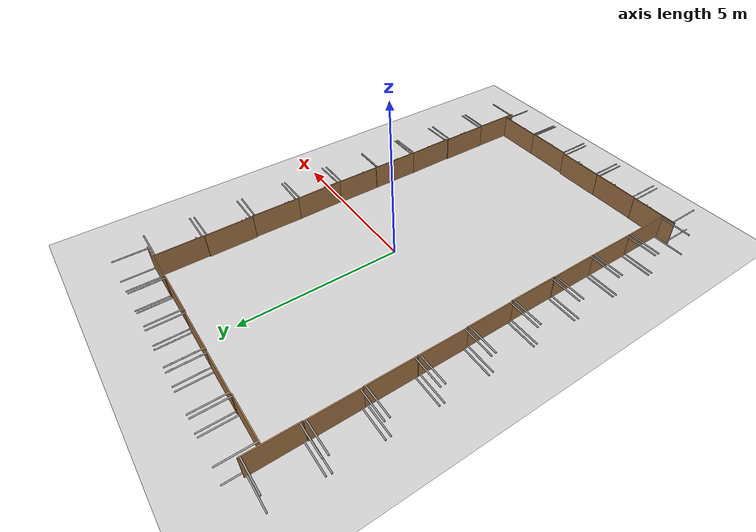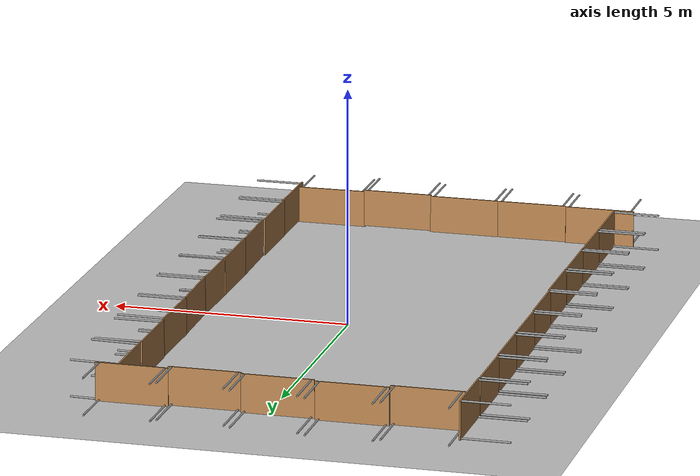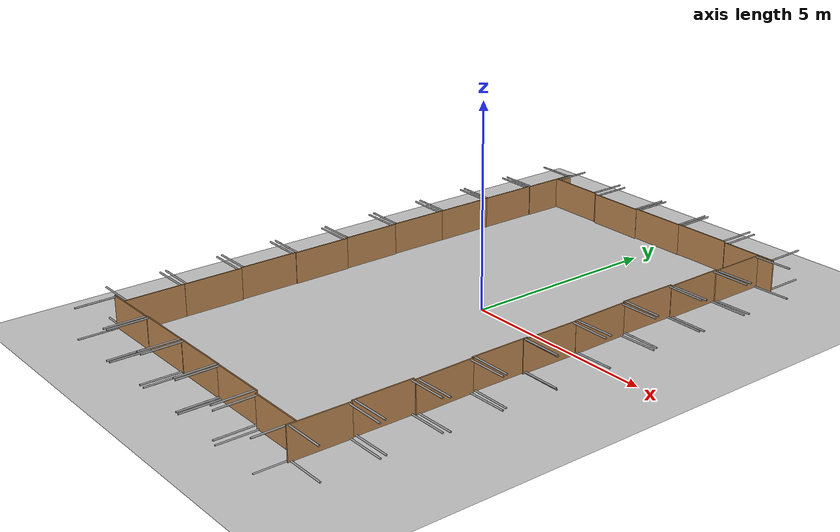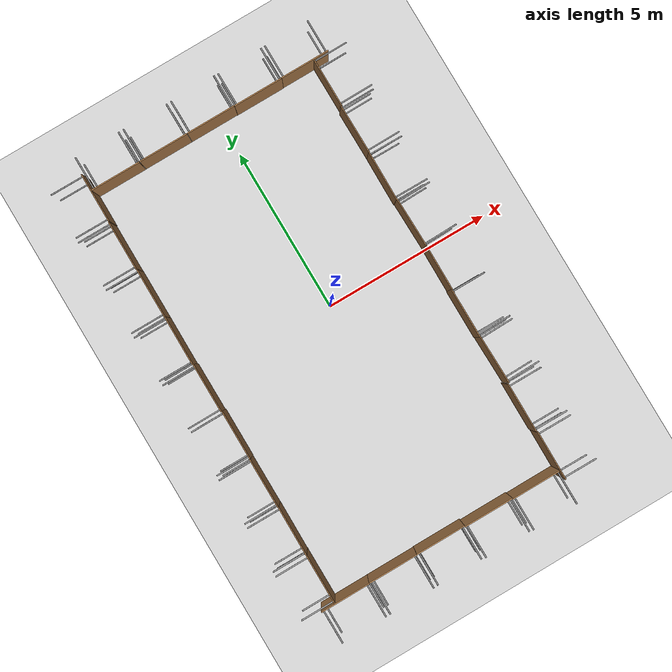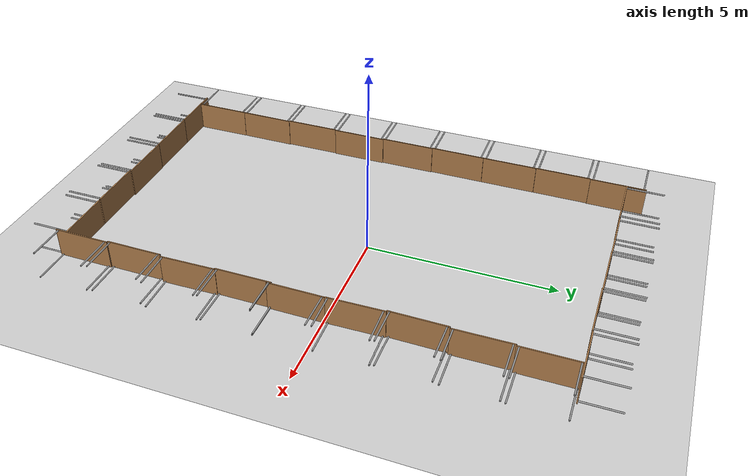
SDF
<sdf version="1.4">
 <world name="default">
  <light name="sun" type="directional">
   <pose>0 0 10 0 -0 0</pose>
   <diffuse>0.8 0.8 0.8 1</diffuse>
   <specular>0.2 0.2 0.2 1</specular>
   <attenuation>
    <range>1000</range>
    <constant>0.9</constant>
    <linear>0.01</linear>
    <quadratic>0.001</quadratic>
   </attenuation>
   <direction>-0.5 0.1 -0.9</direction>
  </light>
  <model name="ground_plane">
   <static>1</static>
   <link name="link">
    <collision name="collision">
     <geometry><plane><normal>0 0 1</normal><size>100 100</size></plane></geometry>
     <surface><friction><ode><mu>100</mu><mu2>50</mu2></ode></friction></surface>
    </collision>
    <visual name="visual">
     <cast_shadows>0</cast_shadows>
     <geometry><plane><normal>0 0 1</normal><size>100 100</size></plane></geometry>
     <material>
      <script><uri>file://media/materials/scripts/gazebo.material</uri><name>Gazebo/Grey</name></script>
     </material>
    </visual>
    <velocity_decay><linear>0</linear><angular>0</angular></velocity_decay>
   </link>
  </model>
  <physics type="ode">
   <max_step_size>0.001</max_step_size>
   <real_time_factor>1</real_time_factor>
   <real_time_update_rate>1000</real_time_update_rate>
   <gravity>0 0 -9.8</gravity>
  </physics>
  <scene><ambient>0.4 0.4 0.4 1</ambient><background>0.7 0.7 0.7 1</background><shadows>1</shadows></scene>
  <spherical_coordinates>
   <surface_model>EARTH_WGS84</surface_model>
   <latitude_deg>0</latitude_deg>
   <longitude_deg>0</longitude_deg>
   <elevation>0</elevation>
   <heading_deg>0</heading_deg>
  </spherical_coordinates>
  <model name="table">
   <static>1</static>
   <link name="link">
    <collision name="surface">
     <pose>0 0 1 0 -0 0</pose>
     <geometry><box><size>1.5 0.8 0.03</size></box></geometry>
     <surface><friction><ode><mu>0.6</mu><mu2>0.6</mu2></ode></friction></surface>
    </collision>
    <visual name="visual1">
     <pose>0 0 1 0 -0 0</pose>
     <geometry><box><size>1.5 0.8 0.03</size></box></geometry>
     <material>
      <script><uri>file://media/materials/scripts/gazebo.material</uri><name>Gazebo/Wood</name></script>
     </material>
    </visual>
    <collision name="front_left_leg">
     <pose>0.68 0.38 0.5 0 -0 0</pose>
     <geometry><cylinder><radius>0.02</radius><length>1</length></cylinder></geometry>
    </collision>
    <visual name="front_left_leg">
     <pose>0.68 0.38 0.5 0 -0 0</pose>
     <geometry><cylinder><radius>0.02</radius><length>1</length></cylinder></geometry>
     <material>
      <script><uri>file://media/materials/scripts/gazebo.material</uri><name>Gazebo/Grey</name></script>
     </material>
    </visual>
    <collision name="front_right_leg">
     <pose>0.68 -0.38 0.5 0 -0 0</pose>
     <geometry><cylinder><radius>0.02</radius><length>1</length></cylinder></geometry>
    </collision>
    <visual name="front_right_leg">
     <pose>0.68 -0.38 0.5 0 -0 0</pose>
     <geometry><cylinder><radius>0.02</radius><length>1</length></cylinder></geometry>
     <material>
      <script><uri>file://media/materials/scripts/gazebo.material</uri><name>Gazebo/Grey</name></script>
     </material>
    </visual>
    <collision name="back_right_leg">
     <pose>-0.68 -0.38 0.5 0 -0 0</pose>
     <geometry><cylinder><radius>0.02</radius><length>1</length></cylinder></geometry>
    </collision>
    <visual name="back_right_leg">
     <pose>-0.68 -0.38 0.5 0 -0 0</pose>
     <geometry><cylinder><radius>0.02</radius><length>1</length></cylinder></geometry>
     <material>
      <script><uri>file://media/materials/scripts/gazebo.material</uri><name>Gazebo/Grey</name></script>
     </material>
    </visual>
    <collision name="back_left_leg">
     <pose>-0.68 0.38 0.5 0 -0 0</pose>
     <geometry><cylinder><radius>0.02</radius><length>1</length></cylinder></geometry>
    </collision>
    <visual name="back_left_leg">
     <pose>-0.68 0.38 0.5 0 -0 0</pose>
     <geometry><cylinder><radius>0.02</radius><length>1</length></cylinder></geometry>
     <material>
      <script><uri>file://media/materials/scripts/gazebo.material</uri><name>Gazebo/Grey</name></script>
     </material>
    </visual>
    <velocity_decay><linear>0</linear><angular>0</angular></velocity_decay>
   </link>
   <pose>-1.72744 7.02472 0.377492 1.56736 -0 0</pose>
  </model>
  <model name="table_0">
   <static>1</static>
   <link name="link">
    <collision name="surface">
     <pose>0 0 1 0 -0 0</pose>
     <geometry><box><size>1.5 0.8 0.03</size></box></geometry>
     <surface><friction><ode><mu>0.6</mu><mu2>0.6</mu2></ode></friction></surface>
    </collision>
    <visual name="visual1">
     <pose>0 0 1 0 -0 0</pose>
     <geometry><box><size>1.5 0.8 0.03</size></box></geometry>
     <material>
      <script><uri>file://media/materials/scripts/gazebo.material</uri><name>Gazebo/Wood</name></script>
     </material>
    </visual>
    <collision name="front_left_leg">
     <pose>0.68 0.38 0.5 0 -0 0</pose>
     <geometry><cylinder><radius>0.02</radius><length>1</length></cylinder></geometry>
    </collision>
    <visual name="front_left_leg">
     <pose>0.68 0.38 0.5 0 -0 0</pose>
     <geometry><cylinder><radius>0.02</radius><length>1</length></cylinder></geometry>
     <material>
      <script><uri>file://media/materials/scripts/gazebo.material</uri><name>Gazebo/Grey</name></script>
     </material>
    </visual>
    <collision name="front_right_leg">
     <pose>0.68 -0.38 0.5 0 -0 0</pose>
     <geometry><cylinder><radius>0.02</radius><length>1</length></cylinder></geometry>
    </collision>
    <visual name="front_right_leg">
     <pose>0.68 -0.38 0.5 0 -0 0</pose>
     <geometry><cylinder><radius>0.02</radius><length>1</length></cylinder></geometry>
     <material>
      <script><uri>file://media/materials/scripts/gazebo.material</uri><name>Gazebo/Grey</name></script>
     </material>
    </visual>
    <collision name="back_right_leg">
     <pose>-0.68 -0.38 0.5 0 -0 0</pose>
     <geometry><cylinder><radius>0.02</radius><length>1</length></cylinder></geometry>
    </collision>
    <visual name="back_right_leg">
     <pose>-0.68 -0.38 0.5 0 -0 0</pose>
     <geometry><cylinder><radius>0.02</radius><length>1</length></cylinder></geometry>
     <material>
      <script><uri>file://media/materials/scripts/gazebo.material</uri><name>Gazebo/Grey</name></script>
     </material>
    </visual>
    <collision name="back_left_leg">
     <pose>-0.68 0.38 0.5 0 -0 0</pose>
     <geometry><cylinder><radius>0.02</radius><length>1</length></cylinder></geometry>
    </collision>
    <visual name="back_left_leg">
     <pose>-0.68 0.38 0.5 0 -0 0</pose>
     <geometry><cylinder><radius>0.02</radius><length>1</length></cylinder></geometry>
     <material>
      <script><uri>file://media/materials/scripts/gazebo.material</uri><name>Gazebo/Grey</name></script>
     </material>
    </visual>
    <velocity_decay><linear>0</linear><angular>0</angular></velocity_decay>
   </link>
   <pose>-0.21834 7.01913 0.401819 1.56825 -0 0</pose>
  </model>
  <model name="table_1">
   <static>1</static>
   <link name="link">
    <collision name="surface">
     <pose>0 0 1 0 -0 0</pose>
     <geometry><box><size>1.5 0.8 0.03</size></box></geometry>
     <surface><friction><ode><mu>0.6</mu><mu2>0.6</mu2></ode></friction></surface>
    </collision>
    <visual name="visual1">
     <pose>0 0 1 0 -0 0</pose>
     <geometry><box><size>1.5 0.8 0.03</size></box></geometry>
     <material>
      <script><uri>file://media/materials/scripts/gazebo.material</uri><name>Gazebo/Wood</name></script>
     </material>
    </visual>
    <collision name="front_left_leg">
     <pose>0.68 0.38 0.5 0 -0 0</pose>
     <geometry><cylinder><radius>0.02</radius><length>1</length></cylinder></geometry>
    </collision>
    <visual name="front_left_leg">
     <pose>0.68 0.38 0.5 0 -0 0</pose>
     <geometry><cylinder><radius>0.02</radius><length>1</length></cylinder></geometry>
     <material>
      <script><uri>file://media/materials/scripts/gazebo.material</uri><name>Gazebo/Grey</name></script>
     </material>
    </visual>
    <collision name="front_right_leg">
     <pose>0.68 -0.38 0.5 0 -0 0</pose>
     <geometry><cylinder><radius>0.02</radius><length>1</length></cylinder></geometry>
    </collision>
    <visual name="front_right_leg">
     <pose>0.68 -0.38 0.5 0 -0 0</pose>
     <geometry><cylinder><radius>0.02</radius><length>1</length></cylinder></geometry>
     <material>
      <script><uri>file://media/materials/scripts/gazebo.material</uri><name>Gazebo/Grey</name></script>
     </material>
    </visual>
    <collision name="back_right_leg">
     <pose>-0.68 -0.38 0.5 0 -0 0</pose>
     <geometry><cylinder><radius>0.02</radius><length>1</length></cylinder></geometry>
    </collision>
    <visual name="back_right_leg">
     <pose>-0.68 -0.38 0.5 0 -0 0</pose>
     <geometry><cylinder><radius>0.02</radius><length>1</length></cylinder></geometry>
     <material>
      <script><uri>file://media/materials/scripts/gazebo.material</uri><name>Gazebo/Grey</name></script>
     </material>
    </visual>
    <collision name="back_left_leg">
     <pose>-0.68 0.38 0.5 0 -0 0</pose>
     <geometry><cylinder><radius>0.02</radius><length>1</length></cylinder></geometry>
    </collision>
    <visual name="back_left_leg">
     <pose>-0.68 0.38 0.5 0 -0 0</pose>
     <geometry><cylinder><radius>0.02</radius><length>1</length></cylinder></geometry>
     <material>
      <script><uri>file://media/materials/scripts/gazebo.material</uri><name>Gazebo/Grey</name></script>
     </material>
    </visual>
    <velocity_decay><linear>0</linear><angular>0</angular></velocity_decay>
   </link>
   <pose>1.27062 7.00509 0.422156 1.5692 -0 0</pose>
  </model>
  <model name="table_2">
   <static>1</static>
   <link name="link">
    <collision name="surface">
     <pose>0 0 1 0 -0 0</pose>
     <geometry><box><size>1.5 0.8 0.03</size></box></geometry>
     <surface><friction><ode><mu>0.6</mu><mu2>0.6</mu2></ode></friction></surface>
    </collision>
    <visual name="visual1">
     <pose>0 0 1 0 -0 0</pose>
     <geometry><box><size>1.5 0.8 0.03</size></box></geometry>
     <material>
      <script><uri>file://media/materials/scripts/gazebo.material</uri><name>Gazebo/Wood</name></script>
     </material>
    </visual>
    <collision name="front_left_leg">
     <pose>0.68 0.38 0.5 0 -0 0</pose>
     <geometry><cylinder><radius>0.02</radius><length>1</length></cylinder></geometry>
    </collision>
    <visual name="front_left_leg">
     <pose>0.68 0.38 0.5 0 -0 0</pose>
     <geometry><cylinder><radius>0.02</radius><length>1</length></cylinder></geometry>
     <material>
      <script><uri>file://media/materials/scripts/gazebo.material</uri><name>Gazebo/Grey</name></script>
     </material>
    </visual>
    <collision name="front_right_leg">
     <pose>0.68 -0.38 0.5 0 -0 0</pose>
     <geometry><cylinder><radius>0.02</radius><length>1</length></cylinder></geometry>
    </collision>
    <visual name="front_right_leg">
     <pose>0.68 -0.38 0.5 0 -0 0</pose>
     <geometry><cylinder><radius>0.02</radius><length>1</length></cylinder></geometry>
     <material>
      <script><uri>file://media/materials/scripts/gazebo.material</uri><name>Gazebo/Grey</name></script>
     </material>
    </visual>
    <collision name="back_right_leg">
     <pose>-0.68 -0.38 0.5 0 -0 0</pose>
     <geometry><cylinder><radius>0.02</radius><length>1</length></cylinder></geometry>
    </collision>
    <visual name="back_right_leg">
     <pose>-0.68 -0.38 0.5 0 -0 0</pose>
     <geometry><cylinder><radius>0.02</radius><length>1</length></cylinder></geometry>
     <material>
      <script><uri>file://media/materials/scripts/gazebo.material</uri><name>Gazebo/Grey</name></script>
     </material>
    </visual>
    <collision name="back_left_leg">
     <pose>-0.68 0.38 0.5 0 -0 0</pose>
     <geometry><cylinder><radius>0.02</radius><length>1</length></cylinder></geometry>
    </collision>
    <visual name="back_left_leg">
     <pose>-0.68 0.38 0.5 0 -0 0</pose>
     <geometry><cylinder><radius>0.02</radius><length>1</length></cylinder></geometry>
     <material>
      <script><uri>file://media/materials/scripts/gazebo.material</uri><name>Gazebo/Grey</name></script>
     </material>
    </visual>
    <velocity_decay><linear>0</linear><angular>0</angular></velocity_decay>
   </link>
   <pose>-3.24093 7.00952 0.41318 1.56982 -0 0</pose>
  </model>
  <model name="table_3">
   <static>1</static>
   <link name="link">
    <collision name="surface">
     <pose>0 0 1 0 -0 0</pose>
     <geometry><box><size>1.5 0.8 0.03</size></box></geometry>
     <surface><friction><ode><mu>0.6</mu><mu2>0.6</mu2></ode></friction></surface>
    </collision>
    <visual name="visual1">
     <pose>0 0 1 0 -0 0</pose>
     <geometry><box><size>1.5 0.8 0.03</size></box></geometry>
     <material>
      <script><uri>file://media/materials/scripts/gazebo.material</uri><name>Gazebo/Wood</name></script>
     </material>
    </visual>
    <collision name="front_left_leg">
     <pose>0.68 0.38 0.5 0 -0 0</pose>
     <geometry><cylinder><radius>0.02</radius><length>1</length></cylinder></geometry>
    </collision>
    <visual name="front_left_leg">
     <pose>0.68 0.38 0.5 0 -0 0</pose>
     <geometry><cylinder><radius>0.02</radius><length>1</length></cylinder></geometry>
     <material>
      <script><uri>file://media/materials/scripts/gazebo.material</uri><name>Gazebo/Grey</name></script>
     </material>
    </visual>
    <collision name="front_right_leg">
     <pose>0.68 -0.38 0.5 0 -0 0</pose>
     <geometry><cylinder><radius>0.02</radius><length>1</length></cylinder></geometry>
    </collision>
    <visual name="front_right_leg">
     <pose>0.68 -0.38 0.5 0 -0 0</pose>
     <geometry><cylinder><radius>0.02</radius><length>1</length></cylinder></geometry>
     <material>
      <script><uri>file://media/materials/scripts/gazebo.material</uri><name>Gazebo/Grey</name></script>
     </material>
    </visual>
    <collision name="back_right_leg">
     <pose>-0.68 -0.38 0.5 0 -0 0</pose>
     <geometry><cylinder><radius>0.02</radius><length>1</length></cylinder></geometry>
    </collision>
    <visual name="back_right_leg">
     <pose>-0.68 -0.38 0.5 0 -0 0</pose>
     <geometry><cylinder><radius>0.02</radius><length>1</length></cylinder></geometry>
     <material>
      <script><uri>file://media/materials/scripts/gazebo.material</uri><name>Gazebo/Grey</name></script>
     </material>
    </visual>
    <collision name="back_left_leg">
     <pose>-0.68 0.38 0.5 0 -0 0</pose>
     <geometry><cylinder><radius>0.02</radius><length>1</length></cylinder></geometry>
    </collision>
    <visual name="back_left_leg">
     <pose>-0.68 0.38 0.5 0 -0 0</pose>
     <geometry><cylinder><radius>0.02</radius><length>1</length></cylinder></geometry>
     <material>
      <script><uri>file://media/materials/scripts/gazebo.material</uri><name>Gazebo/Grey</name></script>
     </material>
    </visual>
    <velocity_decay><linear>0</linear><angular>0</angular></velocity_decay>
   </link>
   <pose>2.76108 7.0224 0.393768 1.57395 -0 0</pose>
  </model>
  <model name="table_4">
   <static>1</static>
   <link name="link">
    <collision name="surface">
     <pose>0 0 1 0 -0 0</pose>
     <geometry><box><size>1.5 0.8 0.03</size></box></geometry>
     <surface><friction><ode><mu>0.6</mu><mu2>0.6</mu2></ode></friction></surface>
    </collision>
    <visual name="visual1">
     <pose>0 0 1 0 -0 0</pose>
     <geometry><box><size>1.5 0.8 0.03</size></box></geometry>
     <material>
      <script><uri>file://media/materials/scripts/gazebo.material</uri><name>Gazebo/Wood</name></script>
     </material>
    </visual>
    <collision name="front_left_leg">
     <pose>0.68 0.38 0.5 0 -0 0</pose>
     <geometry><cylinder><radius>0.02</radius><length>1</length></cylinder></geometry>
    </collision>
    <visual name="front_left_leg">
     <pose>0.68 0.38 0.5 0 -0 0</pose>
     <geometry><cylinder><radius>0.02</radius><length>1</length></cylinder></geometry>
     <material>
      <script><uri>file://media/materials/scripts/gazebo.material</uri><name>Gazebo/Grey</name></script>
     </material>
    </visual>
    <collision name="front_right_leg">
     <pose>0.68 -0.38 0.5 0 -0 0</pose>
     <geometry><cylinder><radius>0.02</radius><length>1</length></cylinder></geometry>
    </collision>
    <visual name="front_right_leg">
     <pose>0.68 -0.38 0.5 0 -0 0</pose>
     <geometry><cylinder><radius>0.02</radius><length>1</length></cylinder></geometry>
     <material>
      <script><uri>file://media/materials/scripts/gazebo.material</uri><name>Gazebo/Grey</name></script>
     </material>
    </visual>
    <collision name="back_right_leg">
     <pose>-0.68 -0.38 0.5 0 -0 0</pose>
     <geometry><cylinder><radius>0.02</radius><length>1</length></cylinder></geometry>
    </collision>
    <visual name="back_right_leg">
     <pose>-0.68 -0.38 0.5 0 -0 0</pose>
     <geometry><cylinder><radius>0.02</radius><length>1</length></cylinder></geometry>
     <material>
      <script><uri>file://media/materials/scripts/gazebo.material</uri><name>Gazebo/Grey</name></script>
     </material>
    </visual>
    <collision name="back_left_leg">
     <pose>-0.68 0.38 0.5 0 -0 0</pose>
     <geometry><cylinder><radius>0.02</radius><length>1</length></cylinder></geometry>
    </collision>
    <visual name="back_left_leg">
     <pose>-0.68 0.38 0.5 0 -0 0</pose>
     <geometry><cylinder><radius>0.02</radius><length>1</length></cylinder></geometry>
     <material>
      <script><uri>file://media/materials/scripts/gazebo.material</uri><name>Gazebo/Grey</name></script>
     </material>
    </visual>
    <velocity_decay><linear>0</linear><angular>0</angular></velocity_decay>
   </link>
   <pose>4.0519 5.27988 0.395375 1.58577 -0 -1.56889</pose>
  </model>
  <model name="table_5">
   <static>1</static>
   <link name="link">
    <collision name="surface">
     <pose>0 0 1 0 -0 0</pose>
     <geometry><box><size>1.5 0.8 0.03</size></box></geometry>
     <surface><friction><ode><mu>0.6</mu><mu2>0.6</mu2></ode></friction></surface>
    </collision>
    <visual name="visual1">
     <pose>0 0 1 0 -0 0</pose>
     <geometry><box><size>1.5 0.8 0.03</size></box></geometry>
     <material>
      <script><uri>file://media/materials/scripts/gazebo.material</uri><name>Gazebo/Wood</name></script>
     </material>
    </visual>
    <collision name="front_left_leg">
     <pose>0.68 0.38 0.5 0 -0 0</pose>
     <geometry><cylinder><radius>0.02</radius><length>1</length></cylinder></geometry>
    </collision>
    <visual name="front_left_leg">
     <pose>0.68 0.38 0.5 0 -0 0</pose>
     <geometry><cylinder><radius>0.02</radius><length>1</length></cylinder></geometry>
     <material>
      <script><uri>file://media/materials/scripts/gazebo.material</uri><name>Gazebo/Grey</name></script>
     </material>
    </visual>
    <collision name="front_right_leg">
     <pose>0.68 -0.38 0.5 0 -0 0</pose>
     <geometry><cylinder><radius>0.02</radius><length>1</length></cylinder></geometry>
    </collision>
    <visual name="front_right_leg">
     <pose>0.68 -0.38 0.5 0 -0 0</pose>
     <geometry><cylinder><radius>0.02</radius><length>1</length></cylinder></geometry>
     <material>
      <script><uri>file://media/materials/scripts/gazebo.material</uri><name>Gazebo/Grey</name></script>
     </material>
    </visual>
    <collision name="back_right_leg">
     <pose>-0.68 -0.38 0.5 0 -0 0</pose>
     <geometry><cylinder><radius>0.02</radius><length>1</length></cylinder></geometry>
    </collision>
    <visual name="back_right_leg">
     <pose>-0.68 -0.38 0.5 0 -0 0</pose>
     <geometry><cylinder><radius>0.02</radius><length>1</length></cylinder></geometry>
     <material>
      <script><uri>file://media/materials/scripts/gazebo.material</uri><name>Gazebo/Grey</name></script>
     </material>
    </visual>
    <collision name="back_left_leg">
     <pose>-0.68 0.38 0.5 0 -0 0</pose>
     <geometry><cylinder><radius>0.02</radius><length>1</length></cylinder></geometry>
    </collision>
    <visual name="back_left_leg">
     <pose>-0.68 0.38 0.5 0 -0 0</pose>
     <geometry><cylinder><radius>0.02</radius><length>1</length></cylinder></geometry>
     <material>
      <script><uri>file://media/materials/scripts/gazebo.material</uri><name>Gazebo/Grey</name></script>
     </material>
    </visual>
    <velocity_decay><linear>0</linear><angular>0</angular></velocity_decay>
   </link>
   <pose>4.02611 3.79466 0.386087 1.56682 -5.55112e-17 -1.564</pose>
  </model>
  <model name="table_6">
   <static>1</static>
   <link name="link">
    <collision name="surface">
     <pose>0 0 1 0 -0 0</pose>
     <geometry><box><size>1.5 0.8 0.03</size></box></geometry>
     <surface><friction><ode><mu>0.6</mu><mu2>0.6</mu2></ode></friction></surface>
    </collision>
    <visual name="visual1">
     <pose>0 0 1 0 -0 0</pose>
     <geometry><box><size>1.5 0.8 0.03</size></box></geometry>
     <material>
      <script><uri>file://media/materials/scripts/gazebo.material</uri><name>Gazebo/Wood</name></script>
     </material>
    </visual>
    <collision name="front_left_leg">
     <pose>0.68 0.38 0.5 0 -0 0</pose>
     <geometry><cylinder><radius>0.02</radius><length>1</length></cylinder></geometry>
    </collision>
    <visual name="front_left_leg">
     <pose>0.68 0.38 0.5 0 -0 0</pose>
     <geometry><cylinder><radius>0.02</radius><length>1</length></cylinder></geometry>
     <material>
      <script><uri>file://media/materials/scripts/gazebo.material</uri><name>Gazebo/Grey</name></script>
     </material>
    </visual>
    <collision name="front_right_leg">
     <pose>0.68 -0.38 0.5 0 -0 0</pose>
     <geometry><cylinder><radius>0.02</radius><length>1</length></cylinder></geometry>
    </collision>
    <visual name="front_right_leg">
     <pose>0.68 -0.38 0.5 0 -0 0</pose>
     <geometry><cylinder><radius>0.02</radius><length>1</length></cylinder></geometry>
     <material>
      <script><uri>file://media/materials/scripts/gazebo.material</uri><name>Gazebo/Grey</name></script>
     </material>
    </visual>
    <collision name="back_right_leg">
     <pose>-0.68 -0.38 0.5 0 -0 0</pose>
     <geometry><cylinder><radius>0.02</radius><length>1</length></cylinder></geometry>
    </collision>
    <visual name="back_right_leg">
     <pose>-0.68 -0.38 0.5 0 -0 0</pose>
     <geometry><cylinder><radius>0.02</radius><length>1</length></cylinder></geometry>
     <material>
      <script><uri>file://media/materials/scripts/gazebo.material</uri><name>Gazebo/Grey</name></script>
     </material>
    </visual>
    <collision name="back_left_leg">
     <pose>-0.68 0.38 0.5 0 -0 0</pose>
     <geometry><cylinder><radius>0.02</radius><length>1</length></cylinder></geometry>
    </collision>
    <visual name="back_left_leg">
     <pose>-0.68 0.38 0.5 0 -0 0</pose>
     <geometry><cylinder><radius>0.02</radius><length>1</length></cylinder></geometry>
     <material>
      <script><uri>file://media/materials/scripts/gazebo.material</uri><name>Gazebo/Grey</name></script>
     </material>
    </visual>
    <velocity_decay><linear>0</linear><angular>0</angular></velocity_decay>
   </link>
   <pose>4.01433 2.28553 0.420375 1.57099 -0 -1.57986</pose>
  </model>
  <model name="table_7">
   <static>1</static>
   <link name="link">
    <collision name="surface">
     <pose>0 0 1 0 -0 0</pose>
     <geometry><box><size>1.5 0.8 0.03</size></box></geometry>
     <surface><friction><ode><mu>0.6</mu><mu2>0.6</mu2></ode></friction></surface>
    </collision>
    <visual name="visual1">
     <pose>0 0 1 0 -0 0</pose>
     <geometry><box><size>1.5 0.8 0.03</size></box></geometry>
     <material>
      <script><uri>file://media/materials/scripts/gazebo.material</uri><name>Gazebo/Wood</name></script>
     </material>
    </visual>
    <collision name="front_left_leg">
     <pose>0.68 0.38 0.5 0 -0 0</pose>
     <geometry><cylinder><radius>0.02</radius><length>1</length></cylinder></geometry>
    </collision>
    <visual name="front_left_leg">
     <pose>0.68 0.38 0.5 0 -0 0</pose>
     <geometry><cylinder><radius>0.02</radius><length>1</length></cylinder></geometry>
     <material>
      <script><uri>file://media/materials/scripts/gazebo.material</uri><name>Gazebo/Grey</name></script>
     </material>
    </visual>
    <collision name="front_right_leg">
     <pose>0.68 -0.38 0.5 0 -0 0</pose>
     <geometry><cylinder><radius>0.02</radius><length>1</length></cylinder></geometry>
    </collision>
    <visual name="front_right_leg">
     <pose>0.68 -0.38 0.5 0 -0 0</pose>
     <geometry><cylinder><radius>0.02</radius><length>1</length></cylinder></geometry>
     <material>
      <script><uri>file://media/materials/scripts/gazebo.material</uri><name>Gazebo/Grey</name></script>
     </material>
    </visual>
    <collision name="back_right_leg">
     <pose>-0.68 -0.38 0.5 0 -0 0</pose>
     <geometry><cylinder><radius>0.02</radius><length>1</length></cylinder></geometry>
    </collision>
    <visual name="back_right_leg">
     <pose>-0.68 -0.38 0.5 0 -0 0</pose>
     <geometry><cylinder><radius>0.02</radius><length>1</length></cylinder></geometry>
     <material>
      <script><uri>file://media/materials/scripts/gazebo.material</uri><name>Gazebo/Grey</name></script>
     </material>
    </visual>
    <collision name="back_left_leg">
     <pose>-0.68 0.38 0.5 0 -0 0</pose>
     <geometry><cylinder><radius>0.02</radius><length>1</length></cylinder></geometry>
    </collision>
    <visual name="back_left_leg">
     <pose>-0.68 0.38 0.5 0 -0 0</pose>
     <geometry><cylinder><radius>0.02</radius><length>1</length></cylinder></geometry>
     <material>
      <script><uri>file://media/materials/scripts/gazebo.material</uri><name>Gazebo/Grey</name></script>
     </material>
    </visual>
    <velocity_decay><linear>0</linear><angular>0</angular></velocity_decay>
   </link>
   <pose>4.03905 0.818093 0.41004 1.57486 -0.000132 -1.55158</pose>
  </model>
  <model name="table_8">
   <static>1</static>
   <link name="link">
    <collision name="surface">
     <pose>0 0 1 0 -0 0</pose>
     <geometry><box><size>1.5 0.8 0.03</size></box></geometry>
     <surface><friction><ode><mu>0.6</mu><mu2>0.6</mu2></ode></friction></surface>
    </collision>
    <visual name="visual1">
     <pose>0 0 1 0 -0 0</pose>
     <geometry><box><size>1.5 0.8 0.03</size></box></geometry>
     <material>
      <script><uri>file://media/materials/scripts/gazebo.material</uri><name>Gazebo/Wood</name></script>
     </material>
    </visual>
    <collision name="front_left_leg">
     <pose>0.68 0.38 0.5 0 -0 0</pose>
     <geometry><cylinder><radius>0.02</radius><length>1</length></cylinder></geometry>
    </collision>
    <visual name="front_left_leg">
     <pose>0.68 0.38 0.5 0 -0 0</pose>
     <geometry><cylinder><radius>0.02</radius><length>1</length></cylinder></geometry>
     <material>
      <script><uri>file://media/materials/scripts/gazebo.material</uri><name>Gazebo/Grey</name></script>
     </material>
    </visual>
    <collision name="front_right_leg">
     <pose>0.68 -0.38 0.5 0 -0 0</pose>
     <geometry><cylinder><radius>0.02</radius><length>1</length></cylinder></geometry>
    </collision>
    <visual name="front_right_leg">
     <pose>0.68 -0.38 0.5 0 -0 0</pose>
     <geometry><cylinder><radius>0.02</radius><length>1</length></cylinder></geometry>
     <material>
      <script><uri>file://media/materials/scripts/gazebo.material</uri><name>Gazebo/Grey</name></script>
     </material>
    </visual>
    <collision name="back_right_leg">
     <pose>-0.68 -0.38 0.5 0 -0 0</pose>
     <geometry><cylinder><radius>0.02</radius><length>1</length></cylinder></geometry>
    </collision>
    <visual name="back_right_leg">
     <pose>-0.68 -0.38 0.5 0 -0 0</pose>
     <geometry><cylinder><radius>0.02</radius><length>1</length></cylinder></geometry>
     <material>
      <script><uri>file://media/materials/scripts/gazebo.material</uri><name>Gazebo/Grey</name></script>
     </material>
    </visual>
    <collision name="back_left_leg">
     <pose>-0.68 0.38 0.5 0 -0 0</pose>
     <geometry><cylinder><radius>0.02</radius><length>1</length></cylinder></geometry>
    </collision>
    <visual name="back_left_leg">
     <pose>-0.68 0.38 0.5 0 -0 0</pose>
     <geometry><cylinder><radius>0.02</radius><length>1</length></cylinder></geometry>
     <material>
      <script><uri>file://media/materials/scripts/gazebo.material</uri><name>Gazebo/Grey</name></script>
     </material>
    </visual>
    <velocity_decay><linear>0</linear><angular>0</angular></velocity_decay>
   </link>
   <pose>4.04656 -0.698243 0.39274 1.5671 -6.2e-05 -1.57612</pose>
  </model>
  <model name="table_9">
   <static>1</static>
   <link name="link">
    <collision name="surface">
     <pose>0 0 1 0 -0 0</pose>
     <geometry><box><size>1.5 0.8 0.03</size></box></geometry>
     <surface><friction><ode><mu>0.6</mu><mu2>0.6</mu2></ode></friction></surface>
    </collision>
    <visual name="visual1">
     <pose>0 0 1 0 -0 0</pose>
     <geometry><box><size>1.5 0.8 0.03</size></box></geometry>
     <material>
      <script><uri>file://media/materials/scripts/gazebo.material</uri><name>Gazebo/Wood</name></script>
     </material>
    </visual>
    <collision name="front_left_leg">
     <pose>0.68 0.38 0.5 0 -0 0</pose>
     <geometry><cylinder><radius>0.02</radius><length>1</length></cylinder></geometry>
    </collision>
    <visual name="front_left_leg">
     <pose>0.68 0.38 0.5 0 -0 0</pose>
     <geometry><cylinder><radius>0.02</radius><length>1</length></cylinder></geometry>
     <material>
      <script><uri>file://media/materials/scripts/gazebo.material</uri><name>Gazebo/Grey</name></script>
     </material>
    </visual>
    <collision name="front_right_leg">
     <pose>0.68 -0.38 0.5 0 -0 0</pose>
     <geometry><cylinder><radius>0.02</radius><length>1</length></cylinder></geometry>
    </collision>
    <visual name="front_right_leg">
     <pose>0.68 -0.38 0.5 0 -0 0</pose>
     <geometry><cylinder><radius>0.02</radius><length>1</length></cylinder></geometry>
     <material>
      <script><uri>file://media/materials/scripts/gazebo.material</uri><name>Gazebo/Grey</name></script>
     </material>
    </visual>
    <collision name="back_right_leg">
     <pose>-0.68 -0.38 0.5 0 -0 0</pose>
     <geometry><cylinder><radius>0.02</radius><length>1</length></cylinder></geometry>
    </collision>
    <visual name="back_right_leg">
     <pose>-0.68 -0.38 0.5 0 -0 0</pose>
     <geometry><cylinder><radius>0.02</radius><length>1</length></cylinder></geometry>
     <material>
      <script><uri>file://media/materials/scripts/gazebo.material</uri><name>Gazebo/Grey</name></script>
     </material>
    </visual>
    <collision name="back_left_leg">
     <pose>-0.68 0.38 0.5 0 -0 0</pose>
     <geometry><cylinder><radius>0.02</radius><length>1</length></cylinder></geometry>
    </collision>
    <visual name="back_left_leg">
     <pose>-0.68 0.38 0.5 0 -0 0</pose>
     <geometry><cylinder><radius>0.02</radius><length>1</length></cylinder></geometry>
     <material>
      <script><uri>file://media/materials/scripts/gazebo.material</uri><name>Gazebo/Grey</name></script>
     </material>
    </visual>
    <velocity_decay><linear>0</linear><angular>0</angular></velocity_decay>
   </link>
   <pose>4.02468 -2.05884 0.410726 1.56766 -0 -1.57067</pose>
  </model>
  <model name="table_10">
   <static>1</static>
   <link name="link">
    <collision name="surface">
     <pose>0 0 1 0 -0 0</pose>
     <geometry><box><size>1.5 0.8 0.03</size></box></geometry>
     <surface><friction><ode><mu>0.6</mu><mu2>0.6</mu2></ode></friction></surface>
    </collision>
    <visual name="visual1">
     <pose>0 0 1 0 -0 0</pose>
     <geometry><box><size>1.5 0.8 0.03</size></box></geometry>
     <material>
      <script><uri>file://media/materials/scripts/gazebo.material</uri><name>Gazebo/Wood</name></script>
     </material>
    </visual>
    <collision name="front_left_leg">
     <pose>0.68 0.38 0.5 0 -0 0</pose>
     <geometry><cylinder><radius>0.02</radius><length>1</length></cylinder></geometry>
    </collision>
    <visual name="front_left_leg">
     <pose>0.68 0.38 0.5 0 -0 0</pose>
     <geometry><cylinder><radius>0.02</radius><length>1</length></cylinder></geometry>
     <material>
      <script><uri>file://media/materials/scripts/gazebo.material</uri><name>Gazebo/Grey</name></script>
     </material>
    </visual>
    <collision name="front_right_leg">
     <pose>0.68 -0.38 0.5 0 -0 0</pose>
     <geometry><cylinder><radius>0.02</radius><length>1</length></cylinder></geometry>
    </collision>
    <visual name="front_right_leg">
     <pose>0.68 -0.38 0.5 0 -0 0</pose>
     <geometry><cylinder><radius>0.02</radius><length>1</length></cylinder></geometry>
     <material>
      <script><uri>file://media/materials/scripts/gazebo.material</uri><name>Gazebo/Grey</name></script>
     </material>
    </visual>
    <collision name="back_right_leg">
     <pose>-0.68 -0.38 0.5 0 -0 0</pose>
     <geometry><cylinder><radius>0.02</radius><length>1</length></cylinder></geometry>
    </collision>
    <visual name="back_right_leg">
     <pose>-0.68 -0.38 0.5 0 -0 0</pose>
     <geometry><cylinder><radius>0.02</radius><length>1</length></cylinder></geometry>
     <material>
      <script><uri>file://media/materials/scripts/gazebo.material</uri><name>Gazebo/Grey</name></script>
     </material>
    </visual>
    <collision name="back_left_leg">
     <pose>-0.68 0.38 0.5 0 -0 0</pose>
     <geometry><cylinder><radius>0.02</radius><length>1</length></cylinder></geometry>
    </collision>
    <visual name="back_left_leg">
     <pose>-0.68 0.38 0.5 0 -0 0</pose>
     <geometry><cylinder><radius>0.02</radius><length>1</length></cylinder></geometry>
     <material>
      <script><uri>file://media/materials/scripts/gazebo.material</uri><name>Gazebo/Grey</name></script>
     </material>
    </visual>
    <velocity_decay><linear>0</linear><angular>0</angular></velocity_decay>
   </link>
   <pose>4.04909 -3.51998 0.39506 1.56955 -0 -1.55255</pose>
  </model>
  <model name="table_11">
   <static>1</static>
   <link name="link">
    <collision name="surface">
     <pose>0 0 1 0 -0 0</pose>
     <geometry><box><size>1.5 0.8 0.03</size></box></geometry>
     <surface><friction><ode><mu>0.6</mu><mu2>0.6</mu2></ode></friction></surface>
    </collision>
    <visual name="visual1">
     <pose>0 0 1 0 -0 0</pose>
     <geometry><box><size>1.5 0.8 0.03</size></box></geometry>
     <material>
      <script><uri>file://media/materials/scripts/gazebo.material</uri><name>Gazebo/Wood</name></script>
     </material>
    </visual>
    <collision name="front_left_leg">
     <pose>0.68 0.38 0.5 0 -0 0</pose>
     <geometry><cylinder><radius>0.02</radius><length>1</length></cylinder></geometry>
    </collision>
    <visual name="front_left_leg">
     <pose>0.68 0.38 0.5 0 -0 0</pose>
     <geometry><cylinder><radius>0.02</radius><length>1</length></cylinder></geometry>
     <material>
      <script><uri>file://media/materials/scripts/gazebo.material</uri><name>Gazebo/Grey</name></script>
     </material>
    </visual>
    <collision name="front_right_leg">
     <pose>0.68 -0.38 0.5 0 -0 0</pose>
     <geometry><cylinder><radius>0.02</radius><length>1</length></cylinder></geometry>
    </collision>
    <visual name="front_right_leg">
     <pose>0.68 -0.38 0.5 0 -0 0</pose>
     <geometry><cylinder><radius>0.02</radius><length>1</length></cylinder></geometry>
     <material>
      <script><uri>file://media/materials/scripts/gazebo.material</uri><name>Gazebo/Grey</name></script>
     </material>
    </visual>
    <collision name="back_right_leg">
     <pose>-0.68 -0.38 0.5 0 -0 0</pose>
     <geometry><cylinder><radius>0.02</radius><length>1</length></cylinder></geometry>
    </collision>
    <visual name="back_right_leg">
     <pose>-0.68 -0.38 0.5 0 -0 0</pose>
     <geometry><cylinder><radius>0.02</radius><length>1</length></cylinder></geometry>
     <material>
      <script><uri>file://media/materials/scripts/gazebo.material</uri><name>Gazebo/Grey</name></script>
     </material>
    </visual>
    <collision name="back_left_leg">
     <pose>-0.68 0.38 0.5 0 -0 0</pose>
     <geometry><cylinder><radius>0.02</radius><length>1</length></cylinder></geometry>
    </collision>
    <visual name="back_left_leg">
     <pose>-0.68 0.38 0.5 0 -0 0</pose>
     <geometry><cylinder><radius>0.02</radius><length>1</length></cylinder></geometry>
     <material>
      <script><uri>file://media/materials/scripts/gazebo.material</uri><name>Gazebo/Grey</name></script>
     </material>
    </visual>
    <velocity_decay><linear>0</linear><angular>0</angular></velocity_decay>
   </link>
   <pose>4.01779 -5.04411 0.415479 1.57516 -0 -1.57394</pose>
  </model>
  <model name="table_12">
   <static>1</static>
   <link name="link">
    <collision name="surface">
     <pose>0 0 1 0 -0 0</pose>
     <geometry><box><size>1.5 0.8 0.03</size></box></geometry>
     <surface><friction><ode><mu>0.6</mu><mu2>0.6</mu2></ode></friction></surface>
    </collision>
    <visual name="visual1">
     <pose>0 0 1 0 -0 0</pose>
     <geometry><box><size>1.5 0.8 0.03</size></box></geometry>
     <material>
      <script><uri>file://media/materials/scripts/gazebo.material</uri><name>Gazebo/Wood</name></script>
     </material>
    </visual>
    <collision name="front_left_leg">
     <pose>0.68 0.38 0.5 0 -0 0</pose>
     <geometry><cylinder><radius>0.02</radius><length>1</length></cylinder></geometry>
    </collision>
    <visual name="front_left_leg">
     <pose>0.68 0.38 0.5 0 -0 0</pose>
     <geometry><cylinder><radius>0.02</radius><length>1</length></cylinder></geometry>
     <material>
      <script><uri>file://media/materials/scripts/gazebo.material</uri><name>Gazebo/Grey</name></script>
     </material>
    </visual>
    <collision name="front_right_leg">
     <pose>0.68 -0.38 0.5 0 -0 0</pose>
     <geometry><cylinder><radius>0.02</radius><length>1</length></cylinder></geometry>
    </collision>
    <visual name="front_right_leg">
     <pose>0.68 -0.38 0.5 0 -0 0</pose>
     <geometry><cylinder><radius>0.02</radius><length>1</length></cylinder></geometry>
     <material>
      <script><uri>file://media/materials/scripts/gazebo.material</uri><name>Gazebo/Grey</name></script>
     </material>
    </visual>
    <collision name="back_right_leg">
     <pose>-0.68 -0.38 0.5 0 -0 0</pose>
     <geometry><cylinder><radius>0.02</radius><length>1</length></cylinder></geometry>
    </collision>
    <visual name="back_right_leg">
     <pose>-0.68 -0.38 0.5 0 -0 0</pose>
     <geometry><cylinder><radius>0.02</radius><length>1</length></cylinder></geometry>
     <material>
      <script><uri>file://media/materials/scripts/gazebo.material</uri><name>Gazebo/Grey</name></script>
     </material>
    </visual>
    <collision name="back_left_leg">
     <pose>-0.68 0.38 0.5 0 -0 0</pose>
     <geometry><cylinder><radius>0.02</radius><length>1</length></cylinder></geometry>
    </collision>
    <visual name="back_left_leg">
     <pose>-0.68 0.38 0.5 0 -0 0</pose>
     <geometry><cylinder><radius>0.02</radius><length>1</length></cylinder></geometry>
     <material>
      <script><uri>file://media/materials/scripts/gazebo.material</uri><name>Gazebo/Grey</name></script>
     </material>
    </visual>
    <velocity_decay><linear>0</linear><angular>0</angular></velocity_decay>
   </link>
   <pose>4.03351 -6.5551 0.399481 1.56946 -0 -1.57791</pose>
  </model>
  <model name="table_13">
   <static>1</static>
   <link name="link">
    <collision name="surface">
     <pose>0 0 1 0 -0 0</pose>
     <geometry><box><size>1.5 0.8 0.03</size></box></geometry>
     <surface><friction><ode><mu>0.6</mu><mu2>0.6</mu2></ode></friction></surface>
    </collision>
    <visual name="visual1">
     <pose>0 0 1 0 -0 0</pose>
     <geometry><box><size>1.5 0.8 0.03</size></box></geometry>
     <material>
      <script><uri>file://media/materials/scripts/gazebo.material</uri><name>Gazebo/Wood</name></script>
     </material>
    </visual>
    <collision name="front_left_leg">
     <pose>0.68 0.38 0.5 0 -0 0</pose>
     <geometry><cylinder><radius>0.02</radius><length>1</length></cylinder></geometry>
    </collision>
    <visual name="front_left_leg">
     <pose>0.68 0.38 0.5 0 -0 0</pose>
     <geometry><cylinder><radius>0.02</radius><length>1</length></cylinder></geometry>
     <material>
      <script><uri>file://media/materials/scripts/gazebo.material</uri><name>Gazebo/Grey</name></script>
     </material>
    </visual>
    <collision name="front_right_leg">
     <pose>0.68 -0.38 0.5 0 -0 0</pose>
     <geometry><cylinder><radius>0.02</radius><length>1</length></cylinder></geometry>
    </collision>
    <visual name="front_right_leg">
     <pose>0.68 -0.38 0.5 0 -0 0</pose>
     <geometry><cylinder><radius>0.02</radius><length>1</length></cylinder></geometry>
     <material>
      <script><uri>file://media/materials/scripts/gazebo.material</uri><name>Gazebo/Grey</name></script>
     </material>
    </visual>
    <collision name="back_right_leg">
     <pose>-0.68 -0.38 0.5 0 -0 0</pose>
     <geometry><cylinder><radius>0.02</radius><length>1</length></cylinder></geometry>
    </collision>
    <visual name="back_right_leg">
     <pose>-0.68 -0.38 0.5 0 -0 0</pose>
     <geometry><cylinder><radius>0.02</radius><length>1</length></cylinder></geometry>
     <material>
      <script><uri>file://media/materials/scripts/gazebo.material</uri><name>Gazebo/Grey</name></script>
     </material>
    </visual>
    <collision name="back_left_leg">
     <pose>-0.68 0.38 0.5 0 -0 0</pose>
     <geometry><cylinder><radius>0.02</radius><length>1</length></cylinder></geometry>
    </collision>
    <visual name="back_left_leg">
     <pose>-0.68 0.38 0.5 0 -0 0</pose>
     <geometry><cylinder><radius>0.02</radius><length>1</length></cylinder></geometry>
     <material>
      <script><uri>file://media/materials/scripts/gazebo.material</uri><name>Gazebo/Grey</name></script>
     </material>
    </visual>
    <velocity_decay><linear>0</linear><angular>0</angular></velocity_decay>
   </link>
   <pose>2.27189 -8.01711 0.366105 -1.56669 0.003542 1.5e-05</pose>
  </model>
  <model name="table_14">
   <static>1</static>
   <link name="link">
    <collision name="surface">
     <pose>0 0 1 0 -0 0</pose>
     <geometry><box><size>1.5 0.8 0.03</size></box></geometry>
     <surface><friction><ode><mu>0.6</mu><mu2>0.6</mu2></ode></friction></surface>
    </collision>
    <visual name="visual1">
     <pose>0 0 1 0 -0 0</pose>
     <geometry><box><size>1.5 0.8 0.03</size></box></geometry>
     <material>
      <script><uri>file://media/materials/scripts/gazebo.material</uri><name>Gazebo/Wood</name></script>
     </material>
    </visual>
    <collision name="front_left_leg">
     <pose>0.68 0.38 0.5 0 -0 0</pose>
     <geometry><cylinder><radius>0.02</radius><length>1</length></cylinder></geometry>
    </collision>
    <visual name="front_left_leg">
     <pose>0.68 0.38 0.5 0 -0 0</pose>
     <geometry><cylinder><radius>0.02</radius><length>1</length></cylinder></geometry>
     <material>
      <script><uri>file://media/materials/scripts/gazebo.material</uri><name>Gazebo/Grey</name></script>
     </material>
    </visual>
    <collision name="front_right_leg">
     <pose>0.68 -0.38 0.5 0 -0 0</pose>
     <geometry><cylinder><radius>0.02</radius><length>1</length></cylinder></geometry>
    </collision>
    <visual name="front_right_leg">
     <pose>0.68 -0.38 0.5 0 -0 0</pose>
     <geometry><cylinder><radius>0.02</radius><length>1</length></cylinder></geometry>
     <material>
      <script><uri>file://media/materials/scripts/gazebo.material</uri><name>Gazebo/Grey</name></script>
     </material>
    </visual>
    <collision name="back_right_leg">
     <pose>-0.68 -0.38 0.5 0 -0 0</pose>
     <geometry><cylinder><radius>0.02</radius><length>1</length></cylinder></geometry>
    </collision>
    <visual name="back_right_leg">
     <pose>-0.68 -0.38 0.5 0 -0 0</pose>
     <geometry><cylinder><radius>0.02</radius><length>1</length></cylinder></geometry>
     <material>
      <script><uri>file://media/materials/scripts/gazebo.material</uri><name>Gazebo/Grey</name></script>
     </material>
    </visual>
    <collision name="back_left_leg">
     <pose>-0.68 0.38 0.5 0 -0 0</pose>
     <geometry><cylinder><radius>0.02</radius><length>1</length></cylinder></geometry>
    </collision>
    <visual name="back_left_leg">
     <pose>-0.68 0.38 0.5 0 -0 0</pose>
     <geometry><cylinder><radius>0.02</radius><length>1</length></cylinder></geometry>
     <material>
      <script><uri>file://media/materials/scripts/gazebo.material</uri><name>Gazebo/Grey</name></script>
     </material>
    </visual>
    <velocity_decay><linear>0</linear><angular>0</angular></velocity_decay>
   </link>
   <pose>0.784446 -7.98443 0.413388 -1.56889 0 0</pose>
  </model>
  <model name="table_15">
   <static>1</static>
   <link name="link">
    <collision name="surface">
     <pose>0 0 1 0 -0 0</pose>
     <geometry><box><size>1.5 0.8 0.03</size></box></geometry>
     <surface><friction><ode><mu>0.6</mu><mu2>0.6</mu2></ode></friction></surface>
    </collision>
    <visual name="visual1">
     <pose>0 0 1 0 -0 0</pose>
     <geometry><box><size>1.5 0.8 0.03</size></box></geometry>
     <material>
      <script><uri>file://media/materials/scripts/gazebo.material</uri><name>Gazebo/Wood</name></script>
     </material>
    </visual>
    <collision name="front_left_leg">
     <pose>0.68 0.38 0.5 0 -0 0</pose>
     <geometry><cylinder><radius>0.02</radius><length>1</length></cylinder></geometry>
    </collision>
    <visual name="front_left_leg">
     <pose>0.68 0.38 0.5 0 -0 0</pose>
     <geometry><cylinder><radius>0.02</radius><length>1</length></cylinder></geometry>
     <material>
      <script><uri>file://media/materials/scripts/gazebo.material</uri><name>Gazebo/Grey</name></script>
     </material>
    </visual>
    <collision name="front_right_leg">
     <pose>0.68 -0.38 0.5 0 -0 0</pose>
     <geometry><cylinder><radius>0.02</radius><length>1</length></cylinder></geometry>
    </collision>
    <visual name="front_right_leg">
     <pose>0.68 -0.38 0.5 0 -0 0</pose>
     <geometry><cylinder><radius>0.02</radius><length>1</length></cylinder></geometry>
     <material>
      <script><uri>file://media/materials/scripts/gazebo.material</uri><name>Gazebo/Grey</name></script>
     </material>
    </visual>
    <collision name="back_right_leg">
     <pose>-0.68 -0.38 0.5 0 -0 0</pose>
     <geometry><cylinder><radius>0.02</radius><length>1</length></cylinder></geometry>
    </collision>
    <visual name="back_right_leg">
     <pose>-0.68 -0.38 0.5 0 -0 0</pose>
     <geometry><cylinder><radius>0.02</radius><length>1</length></cylinder></geometry>
     <material>
      <script><uri>file://media/materials/scripts/gazebo.material</uri><name>Gazebo/Grey</name></script>
     </material>
    </visual>
    <collision name="back_left_leg">
     <pose>-0.68 0.38 0.5 0 -0 0</pose>
     <geometry><cylinder><radius>0.02</radius><length>1</length></cylinder></geometry>
    </collision>
    <visual name="back_left_leg">
     <pose>-0.68 0.38 0.5 0 -0 0</pose>
     <geometry><cylinder><radius>0.02</radius><length>1</length></cylinder></geometry>
     <material>
      <script><uri>file://media/materials/scripts/gazebo.material</uri><name>Gazebo/Grey</name></script>
     </material>
    </visual>
    <velocity_decay><linear>0</linear><angular>0</angular></velocity_decay>
   </link>
   <pose>-0.704425 -7.95797 0.394985 -1.56648 0 0</pose>
  </model>
  <model name="table_16">
   <static>1</static>
   <link name="link">
    <collision name="surface">
     <pose>0 0 1 0 -0 0</pose>
     <geometry><box><size>1.5 0.8 0.03</size></box></geometry>
     <surface><friction><ode><mu>0.6</mu><mu2>0.6</mu2></ode></friction></surface>
    </collision>
    <visual name="visual1">
     <pose>0 0 1 0 -0 0</pose>
     <geometry><box><size>1.5 0.8 0.03</size></box></geometry>
     <material>
      <script><uri>file://media/materials/scripts/gazebo.material</uri><name>Gazebo/Wood</name></script>
     </material>
    </visual>
    <collision name="front_left_leg">
     <pose>0.68 0.38 0.5 0 -0 0</pose>
     <geometry><cylinder><radius>0.02</radius><length>1</length></cylinder></geometry>
    </collision>
    <visual name="front_left_leg">
     <pose>0.68 0.38 0.5 0 -0 0</pose>
     <geometry><cylinder><radius>0.02</radius><length>1</length></cylinder></geometry>
     <material>
      <script><uri>file://media/materials/scripts/gazebo.material</uri><name>Gazebo/Grey</name></script>
     </material>
    </visual>
    <collision name="front_right_leg">
     <pose>0.68 -0.38 0.5 0 -0 0</pose>
     <geometry><cylinder><radius>0.02</radius><length>1</length></cylinder></geometry>
    </collision>
    <visual name="front_right_leg">
     <pose>0.68 -0.38 0.5 0 -0 0</pose>
     <geometry><cylinder><radius>0.02</radius><length>1</length></cylinder></geometry>
     <material>
      <script><uri>file://media/materials/scripts/gazebo.material</uri><name>Gazebo/Grey</name></script>
     </material>
    </visual>
    <collision name="back_right_leg">
     <pose>-0.68 -0.38 0.5 0 -0 0</pose>
     <geometry><cylinder><radius>0.02</radius><length>1</length></cylinder></geometry>
    </collision>
    <visual name="back_right_leg">
     <pose>-0.68 -0.38 0.5 0 -0 0</pose>
     <geometry><cylinder><radius>0.02</radius><length>1</length></cylinder></geometry>
     <material>
      <script><uri>file://media/materials/scripts/gazebo.material</uri><name>Gazebo/Grey</name></script>
     </material>
    </visual>
    <collision name="back_left_leg">
     <pose>-0.68 0.38 0.5 0 -0 0</pose>
     <geometry><cylinder><radius>0.02</radius><length>1</length></cylinder></geometry>
    </collision>
    <visual name="back_left_leg">
     <pose>-0.68 0.38 0.5 0 -0 0</pose>
     <geometry><cylinder><radius>0.02</radius><length>1</length></cylinder></geometry>
     <material>
      <script><uri>file://media/materials/scripts/gazebo.material</uri><name>Gazebo/Grey</name></script>
     </material>
    </visual>
    <velocity_decay><linear>0</linear><angular>0</angular></velocity_decay>
   </link>
   <pose>-2.20567 -7.96485 0.402156 -1.57426 0 0</pose>
  </model>
  <model name="table_17">
   <static>1</static>
   <link name="link">
    <collision name="surface">
     <pose>0 0 1 0 -0 0</pose>
     <geometry><box><size>1.5 0.8 0.03</size></box></geometry>
     <surface><friction><ode><mu>0.6</mu><mu2>0.6</mu2></ode></friction></surface>
    </collision>
    <visual name="visual1">
     <pose>0 0 1 0 -0 0</pose>
     <geometry><box><size>1.5 0.8 0.03</size></box></geometry>
     <material>
      <script><uri>file://media/materials/scripts/gazebo.material</uri><name>Gazebo/Wood</name></script>
     </material>
    </visual>
    <collision name="front_left_leg">
     <pose>0.68 0.38 0.5 0 -0 0</pose>
     <geometry><cylinder><radius>0.02</radius><length>1</length></cylinder></geometry>
    </collision>
    <visual name="front_left_leg">
     <pose>0.68 0.38 0.5 0 -0 0</pose>
     <geometry><cylinder><radius>0.02</radius><length>1</length></cylinder></geometry>
     <material>
      <script><uri>file://media/materials/scripts/gazebo.material</uri><name>Gazebo/Grey</name></script>
     </material>
    </visual>
    <collision name="front_right_leg">
     <pose>0.68 -0.38 0.5 0 -0 0</pose>
     <geometry><cylinder><radius>0.02</radius><length>1</length></cylinder></geometry>
    </collision>
    <visual name="front_right_leg">
     <pose>0.68 -0.38 0.5 0 -0 0</pose>
     <geometry><cylinder><radius>0.02</radius><length>1</length></cylinder></geometry>
     <material>
      <script><uri>file://media/materials/scripts/gazebo.material</uri><name>Gazebo/Grey</name></script>
     </material>
    </visual>
    <collision name="back_right_leg">
     <pose>-0.68 -0.38 0.5 0 -0 0</pose>
     <geometry><cylinder><radius>0.02</radius><length>1</length></cylinder></geometry>
    </collision>
    <visual name="back_right_leg">
     <pose>-0.68 -0.38 0.5 0 -0 0</pose>
     <geometry><cylinder><radius>0.02</radius><length>1</length></cylinder></geometry>
     <material>
      <script><uri>file://media/materials/scripts/gazebo.material</uri><name>Gazebo/Grey</name></script>
     </material>
    </visual>
    <collision name="back_left_leg">
     <pose>-0.68 0.38 0.5 0 -0 0</pose>
     <geometry><cylinder><radius>0.02</radius><length>1</length></cylinder></geometry>
    </collision>
    <visual name="back_left_leg">
     <pose>-0.68 0.38 0.5 0 -0 0</pose>
     <geometry><cylinder><radius>0.02</radius><length>1</length></cylinder></geometry>
     <material>
      <script><uri>file://media/materials/scripts/gazebo.material</uri><name>Gazebo/Grey</name></script>
     </material>
    </visual>
    <velocity_decay><linear>0</linear><angular>0</angular></velocity_decay>
   </link>
   <pose>-3.70229 -7.97253 0.38403 -1.56895 0 0</pose>
  </model>
  <model name="table_18">
   <static>1</static>
   <link name="link">
    <collision name="surface">
     <pose>0 0 1 0 -0 0</pose>
     <geometry><box><size>1.5 0.8 0.03</size></box></geometry>
     <surface><friction><ode><mu>0.6</mu><mu2>0.6</mu2></ode></friction></surface>
    </collision>
    <visual name="visual1">
     <pose>0 0 1 0 -0 0</pose>
     <geometry><box><size>1.5 0.8 0.03</size></box></geometry>
     <material>
      <script><uri>file://media/materials/scripts/gazebo.material</uri><name>Gazebo/Wood</name></script>
     </material>
    </visual>
    <collision name="front_left_leg">
     <pose>0.68 0.38 0.5 0 -0 0</pose>
     <geometry><cylinder><radius>0.02</radius><length>1</length></cylinder></geometry>
    </collision>
    <visual name="front_left_leg">
     <pose>0.68 0.38 0.5 0 -0 0</pose>
     <geometry><cylinder><radius>0.02</radius><length>1</length></cylinder></geometry>
     <material>
      <script><uri>file://media/materials/scripts/gazebo.material</uri><name>Gazebo/Grey</name></script>
     </material>
    </visual>
    <collision name="front_right_leg">
     <pose>0.68 -0.38 0.5 0 -0 0</pose>
     <geometry><cylinder><radius>0.02</radius><length>1</length></cylinder></geometry>
    </collision>
    <visual name="front_right_leg">
     <pose>0.68 -0.38 0.5 0 -0 0</pose>
     <geometry><cylinder><radius>0.02</radius><length>1</length></cylinder></geometry>
     <material>
      <script><uri>file://media/materials/scripts/gazebo.material</uri><name>Gazebo/Grey</name></script>
     </material>
    </visual>
    <collision name="back_right_leg">
     <pose>-0.68 -0.38 0.5 0 -0 0</pose>
     <geometry><cylinder><radius>0.02</radius><length>1</length></cylinder></geometry>
    </collision>
    <visual name="back_right_leg">
     <pose>-0.68 -0.38 0.5 0 -0 0</pose>
     <geometry><cylinder><radius>0.02</radius><length>1</length></cylinder></geometry>
     <material>
      <script><uri>file://media/materials/scripts/gazebo.material</uri><name>Gazebo/Grey</name></script>
     </material>
    </visual>
    <collision name="back_left_leg">
     <pose>-0.68 0.38 0.5 0 -0 0</pose>
     <geometry><cylinder><radius>0.02</radius><length>1</length></cylinder></geometry>
    </collision>
    <visual name="back_left_leg">
     <pose>-0.68 0.38 0.5 0 -0 0</pose>
     <geometry><cylinder><radius>0.02</radius><length>1</length></cylinder></geometry>
     <material>
      <script><uri>file://media/materials/scripts/gazebo.material</uri><name>Gazebo/Grey</name></script>
     </material>
    </visual>
    <velocity_decay><linear>0</linear><angular>0</angular></velocity_decay>
   </link>
   <pose>-5.0211 -6.21216 0.379302 1.5661 6.4e-05 1.57028</pose>
  </model>
  <model name="table_19">
   <static>1</static>
   <link name="link">
    <collision name="surface">
     <pose>0 0 1 0 -0 0</pose>
     <geometry><box><size>1.5 0.8 0.03</size></box></geometry>
     <surface><friction><ode><mu>0.6</mu><mu2>0.6</mu2></ode></friction></surface>
    </collision>
    <visual name="visual1">
     <pose>0 0 1 0 -0 0</pose>
     <geometry><box><size>1.5 0.8 0.03</size></box></geometry>
     <material>
      <script><uri>file://media/materials/scripts/gazebo.material</uri><name>Gazebo/Wood</name></script>
     </material>
    </visual>
    <collision name="front_left_leg">
     <pose>0.68 0.38 0.5 0 -0 0</pose>
     <geometry><cylinder><radius>0.02</radius><length>1</length></cylinder></geometry>
    </collision>
    <visual name="front_left_leg">
     <pose>0.68 0.38 0.5 0 -0 0</pose>
     <geometry><cylinder><radius>0.02</radius><length>1</length></cylinder></geometry>
     <material>
      <script><uri>file://media/materials/scripts/gazebo.material</uri><name>Gazebo/Grey</name></script>
     </material>
    </visual>
    <collision name="front_right_leg">
     <pose>0.68 -0.38 0.5 0 -0 0</pose>
     <geometry><cylinder><radius>0.02</radius><length>1</length></cylinder></geometry>
    </collision>
    <visual name="front_right_leg">
     <pose>0.68 -0.38 0.5 0 -0 0</pose>
     <geometry><cylinder><radius>0.02</radius><length>1</length></cylinder></geometry>
     <material>
      <script><uri>file://media/materials/scripts/gazebo.material</uri><name>Gazebo/Grey</name></script>
     </material>
    </visual>
    <collision name="back_right_leg">
     <pose>-0.68 -0.38 0.5 0 -0 0</pose>
     <geometry><cylinder><radius>0.02</radius><length>1</length></cylinder></geometry>
    </collision>
    <visual name="back_right_leg">
     <pose>-0.68 -0.38 0.5 0 -0 0</pose>
     <geometry><cylinder><radius>0.02</radius><length>1</length></cylinder></geometry>
     <material>
      <script><uri>file://media/materials/scripts/gazebo.material</uri><name>Gazebo/Grey</name></script>
     </material>
    </visual>
    <collision name="back_left_leg">
     <pose>-0.68 0.38 0.5 0 -0 0</pose>
     <geometry><cylinder><radius>0.02</radius><length>1</length></cylinder></geometry>
    </collision>
    <visual name="back_left_leg">
     <pose>-0.68 0.38 0.5 0 -0 0</pose>
     <geometry><cylinder><radius>0.02</radius><length>1</length></cylinder></geometry>
     <material>
      <script><uri>file://media/materials/scripts/gazebo.material</uri><name>Gazebo/Grey</name></script>
     </material>
    </visual>
    <velocity_decay><linear>0</linear><angular>0</angular></velocity_decay>
   </link>
   <pose>-5.01716 -4.70505 0.388077 1.57506 8.5e-05 1.56417</pose>
  </model>
  <model name="table_20">
   <static>1</static>
   <link name="link">
    <collision name="surface">
     <pose>0 0 1 0 -0 0</pose>
     <geometry><box><size>1.5 0.8 0.03</size></box></geometry>
     <surface><friction><ode><mu>0.6</mu><mu2>0.6</mu2></ode></friction></surface>
    </collision>
    <visual name="visual1">
     <pose>0 0 1 0 -0 0</pose>
     <geometry><box><size>1.5 0.8 0.03</size></box></geometry>
     <material>
      <script><uri>file://media/materials/scripts/gazebo.material</uri><name>Gazebo/Wood</name></script>
     </material>
    </visual>
    <collision name="front_left_leg">
     <pose>0.68 0.38 0.5 0 -0 0</pose>
     <geometry><cylinder><radius>0.02</radius><length>1</length></cylinder></geometry>
    </collision>
    <visual name="front_left_leg">
     <pose>0.68 0.38 0.5 0 -0 0</pose>
     <geometry><cylinder><radius>0.02</radius><length>1</length></cylinder></geometry>
     <material>
      <script><uri>file://media/materials/scripts/gazebo.material</uri><name>Gazebo/Grey</name></script>
     </material>
    </visual>
    <collision name="front_right_leg">
     <pose>0.68 -0.38 0.5 0 -0 0</pose>
     <geometry><cylinder><radius>0.02</radius><length>1</length></cylinder></geometry>
    </collision>
    <visual name="front_right_leg">
     <pose>0.68 -0.38 0.5 0 -0 0</pose>
     <geometry><cylinder><radius>0.02</radius><length>1</length></cylinder></geometry>
     <material>
      <script><uri>file://media/materials/scripts/gazebo.material</uri><name>Gazebo/Grey</name></script>
     </material>
    </visual>
    <collision name="back_right_leg">
     <pose>-0.68 -0.38 0.5 0 -0 0</pose>
     <geometry><cylinder><radius>0.02</radius><length>1</length></cylinder></geometry>
    </collision>
    <visual name="back_right_leg">
     <pose>-0.68 -0.38 0.5 0 -0 0</pose>
     <geometry><cylinder><radius>0.02</radius><length>1</length></cylinder></geometry>
     <material>
      <script><uri>file://media/materials/scripts/gazebo.material</uri><name>Gazebo/Grey</name></script>
     </material>
    </visual>
    <collision name="back_left_leg">
     <pose>-0.68 0.38 0.5 0 -0 0</pose>
     <geometry><cylinder><radius>0.02</radius><length>1</length></cylinder></geometry>
    </collision>
    <visual name="back_left_leg">
     <pose>-0.68 0.38 0.5 0 -0 0</pose>
     <geometry><cylinder><radius>0.02</radius><length>1</length></cylinder></geometry>
     <material>
      <script><uri>file://media/materials/scripts/gazebo.material</uri><name>Gazebo/Grey</name></script>
     </material>
    </visual>
    <velocity_decay><linear>0</linear><angular>0</angular></velocity_decay>
   </link>
   <pose>-5.01654 -3.20971 0.39606 1.56895 2e-05 1.57067</pose>
  </model>
  <model name="table_21">
   <static>1</static>
   <link name="link">
    <collision name="surface">
     <pose>0 0 1 0 -0 0</pose>
     <geometry><box><size>1.5 0.8 0.03</size></box></geometry>
     <surface><friction><ode><mu>0.6</mu><mu2>0.6</mu2></ode></friction></surface>
    </collision>
    <visual name="visual1">
     <pose>0 0 1 0 -0 0</pose>
     <geometry><box><size>1.5 0.8 0.03</size></box></geometry>
     <material>
      <script><uri>file://media/materials/scripts/gazebo.material</uri><name>Gazebo/Wood</name></script>
     </material>
    </visual>
    <collision name="front_left_leg">
     <pose>0.68 0.38 0.5 0 -0 0</pose>
     <geometry><cylinder><radius>0.02</radius><length>1</length></cylinder></geometry>
    </collision>
    <visual name="front_left_leg">
     <pose>0.68 0.38 0.5 0 -0 0</pose>
     <geometry><cylinder><radius>0.02</radius><length>1</length></cylinder></geometry>
     <material>
      <script><uri>file://media/materials/scripts/gazebo.material</uri><name>Gazebo/Grey</name></script>
     </material>
    </visual>
    <collision name="front_right_leg">
     <pose>0.68 -0.38 0.5 0 -0 0</pose>
     <geometry><cylinder><radius>0.02</radius><length>1</length></cylinder></geometry>
    </collision>
    <visual name="front_right_leg">
     <pose>0.68 -0.38 0.5 0 -0 0</pose>
     <geometry><cylinder><radius>0.02</radius><length>1</length></cylinder></geometry>
     <material>
      <script><uri>file://media/materials/scripts/gazebo.material</uri><name>Gazebo/Grey</name></script>
     </material>
    </visual>
    <collision name="back_right_leg">
     <pose>-0.68 -0.38 0.5 0 -0 0</pose>
     <geometry><cylinder><radius>0.02</radius><length>1</length></cylinder></geometry>
    </collision>
    <visual name="back_right_leg">
     <pose>-0.68 -0.38 0.5 0 -0 0</pose>
     <geometry><cylinder><radius>0.02</radius><length>1</length></cylinder></geometry>
     <material>
      <script><uri>file://media/materials/scripts/gazebo.material</uri><name>Gazebo/Grey</name></script>
     </material>
    </visual>
    <collision name="back_left_leg">
     <pose>-0.68 0.38 0.5 0 -0 0</pose>
     <geometry><cylinder><radius>0.02</radius><length>1</length></cylinder></geometry>
    </collision>
    <visual name="back_left_leg">
     <pose>-0.68 0.38 0.5 0 -0 0</pose>
     <geometry><cylinder><radius>0.02</radius><length>1</length></cylinder></geometry>
     <material>
      <script><uri>file://media/materials/scripts/gazebo.material</uri><name>Gazebo/Grey</name></script>
     </material>
    </visual>
    <velocity_decay><linear>0</linear><angular>0</angular></velocity_decay>
   </link>
   <pose>-5.00469 -1.71219 0.394164 1.57272 1.8e-05 1.56974</pose>
  </model>
  <model name="table_22">
   <static>1</static>
   <link name="link">
    <collision name="surface">
     <pose>0 0 1 0 -0 0</pose>
     <geometry><box><size>1.5 0.8 0.03</size></box></geometry>
     <surface><friction><ode><mu>0.6</mu><mu2>0.6</mu2></ode></friction></surface>
    </collision>
    <visual name="visual1">
     <pose>0 0 1 0 -0 0</pose>
     <geometry><box><size>1.5 0.8 0.03</size></box></geometry>
     <material>
      <script><uri>file://media/materials/scripts/gazebo.material</uri><name>Gazebo/Wood</name></script>
     </material>
    </visual>
    <collision name="front_left_leg">
     <pose>0.68 0.38 0.5 0 -0 0</pose>
     <geometry><cylinder><radius>0.02</radius><length>1</length></cylinder></geometry>
    </collision>
    <visual name="front_left_leg">
     <pose>0.68 0.38 0.5 0 -0 0</pose>
     <geometry><cylinder><radius>0.02</radius><length>1</length></cylinder></geometry>
     <material>
      <script><uri>file://media/materials/scripts/gazebo.material</uri><name>Gazebo/Grey</name></script>
     </material>
    </visual>
    <collision name="front_right_leg">
     <pose>0.68 -0.38 0.5 0 -0 0</pose>
     <geometry><cylinder><radius>0.02</radius><length>1</length></cylinder></geometry>
    </collision>
    <visual name="front_right_leg">
     <pose>0.68 -0.38 0.5 0 -0 0</pose>
     <geometry><cylinder><radius>0.02</radius><length>1</length></cylinder></geometry>
     <material>
      <script><uri>file://media/materials/scripts/gazebo.material</uri><name>Gazebo/Grey</name></script>
     </material>
    </visual>
    <collision name="back_right_leg">
     <pose>-0.68 -0.38 0.5 0 -0 0</pose>
     <geometry><cylinder><radius>0.02</radius><length>1</length></cylinder></geometry>
    </collision>
    <visual name="back_right_leg">
     <pose>-0.68 -0.38 0.5 0 -0 0</pose>
     <geometry><cylinder><radius>0.02</radius><length>1</length></cylinder></geometry>
     <material>
      <script><uri>file://media/materials/scripts/gazebo.material</uri><name>Gazebo/Grey</name></script>
     </material>
    </visual>
    <collision name="back_left_leg">
     <pose>-0.68 0.38 0.5 0 -0 0</pose>
     <geometry><cylinder><radius>0.02</radius><length>1</length></cylinder></geometry>
    </collision>
    <visual name="back_left_leg">
     <pose>-0.68 0.38 0.5 0 -0 0</pose>
     <geometry><cylinder><radius>0.02</radius><length>1</length></cylinder></geometry>
     <material>
      <script><uri>file://media/materials/scripts/gazebo.material</uri><name>Gazebo/Grey</name></script>
     </material>
    </visual>
    <velocity_decay><linear>0</linear><angular>0</angular></velocity_decay>
   </link>
   <pose>-5.02461 -0.226551 0.392523 1.56776 3.8e-05 1.57174</pose>
  </model>
  <model name="table_23">
   <static>1</static>
   <link name="link">
    <collision name="surface">
     <pose>0 0 1 0 -0 0</pose>
     <geometry><box><size>1.5 0.8 0.03</size></box></geometry>
     <surface><friction><ode><mu>0.6</mu><mu2>0.6</mu2></ode></friction></surface>
    </collision>
    <visual name="visual1">
     <pose>0 0 1 0 -0 0</pose>
     <geometry><box><size>1.5 0.8 0.03</size></box></geometry>
     <material>
      <script><uri>file://media/materials/scripts/gazebo.material</uri><name>Gazebo/Wood</name></script>
     </material>
    </visual>
    <collision name="front_left_leg">
     <pose>0.68 0.38 0.5 0 -0 0</pose>
     <geometry><cylinder><radius>0.02</radius><length>1</length></cylinder></geometry>
    </collision>
    <visual name="front_left_leg">
     <pose>0.68 0.38 0.5 0 -0 0</pose>
     <geometry><cylinder><radius>0.02</radius><length>1</length></cylinder></geometry>
     <material>
      <script><uri>file://media/materials/scripts/gazebo.material</uri><name>Gazebo/Grey</name></script>
     </material>
    </visual>
    <collision name="front_right_leg">
     <pose>0.68 -0.38 0.5 0 -0 0</pose>
     <geometry><cylinder><radius>0.02</radius><length>1</length></cylinder></geometry>
    </collision>
    <visual name="front_right_leg">
     <pose>0.68 -0.38 0.5 0 -0 0</pose>
     <geometry><cylinder><radius>0.02</radius><length>1</length></cylinder></geometry>
     <material>
      <script><uri>file://media/materials/scripts/gazebo.material</uri><name>Gazebo/Grey</name></script>
     </material>
    </visual>
    <collision name="back_right_leg">
     <pose>-0.68 -0.38 0.5 0 -0 0</pose>
     <geometry><cylinder><radius>0.02</radius><length>1</length></cylinder></geometry>
    </collision>
    <visual name="back_right_leg">
     <pose>-0.68 -0.38 0.5 0 -0 0</pose>
     <geometry><cylinder><radius>0.02</radius><length>1</length></cylinder></geometry>
     <material>
      <script><uri>file://media/materials/scripts/gazebo.material</uri><name>Gazebo/Grey</name></script>
     </material>
    </visual>
    <collision name="back_left_leg">
     <pose>-0.68 0.38 0.5 0 -0 0</pose>
     <geometry><cylinder><radius>0.02</radius><length>1</length></cylinder></geometry>
    </collision>
    <visual name="back_left_leg">
     <pose>-0.68 0.38 0.5 0 -0 0</pose>
     <geometry><cylinder><radius>0.02</radius><length>1</length></cylinder></geometry>
     <material>
      <script><uri>file://media/materials/scripts/gazebo.material</uri><name>Gazebo/Grey</name></script>
     </material>
    </visual>
    <velocity_decay><linear>0</linear><angular>0</angular></velocity_decay>
   </link>
   <pose>-5.03967 1.27996 0.400284 1.57418 -5.55112e-17 1.56558</pose>
  </model>
  <model name="table_24">
   <static>1</static>
   <link name="link">
    <collision name="surface">
     <pose>0 0 1 0 -0 0</pose>
     <geometry><box><size>1.5 0.8 0.03</size></box></geometry>
     <surface><friction><ode><mu>0.6</mu><mu2>0.6</mu2></ode></friction></surface>
    </collision>
    <visual name="visual1">
     <pose>0 0 1 0 -0 0</pose>
     <geometry><box><size>1.5 0.8 0.03</size></box></geometry>
     <material>
      <script><uri>file://media/materials/scripts/gazebo.material</uri><name>Gazebo/Wood</name></script>
     </material>
    </visual>
    <collision name="front_left_leg">
     <pose>0.68 0.38 0.5 0 -0 0</pose>
     <geometry><cylinder><radius>0.02</radius><length>1</length></cylinder></geometry>
    </collision>
    <visual name="front_left_leg">
     <pose>0.68 0.38 0.5 0 -0 0</pose>
     <geometry><cylinder><radius>0.02</radius><length>1</length></cylinder></geometry>
     <material>
      <script><uri>file://media/materials/scripts/gazebo.material</uri><name>Gazebo/Grey</name></script>
     </material>
    </visual>
    <collision name="front_right_leg">
     <pose>0.68 -0.38 0.5 0 -0 0</pose>
     <geometry><cylinder><radius>0.02</radius><length>1</length></cylinder></geometry>
    </collision>
    <visual name="front_right_leg">
     <pose>0.68 -0.38 0.5 0 -0 0</pose>
     <geometry><cylinder><radius>0.02</radius><length>1</length></cylinder></geometry>
     <material>
      <script><uri>file://media/materials/scripts/gazebo.material</uri><name>Gazebo/Grey</name></script>
     </material>
    </visual>
    <collision name="back_right_leg">
     <pose>-0.68 -0.38 0.5 0 -0 0</pose>
     <geometry><cylinder><radius>0.02</radius><length>1</length></cylinder></geometry>
    </collision>
    <visual name="back_right_leg">
     <pose>-0.68 -0.38 0.5 0 -0 0</pose>
     <geometry><cylinder><radius>0.02</radius><length>1</length></cylinder></geometry>
     <material>
      <script><uri>file://media/materials/scripts/gazebo.material</uri><name>Gazebo/Grey</name></script>
     </material>
    </visual>
    <collision name="back_left_leg">
     <pose>-0.68 0.38 0.5 0 -0 0</pose>
     <geometry><cylinder><radius>0.02</radius><length>1</length></cylinder></geometry>
    </collision>
    <visual name="back_left_leg">
     <pose>-0.68 0.38 0.5 0 -0 0</pose>
     <geometry><cylinder><radius>0.02</radius><length>1</length></cylinder></geometry>
     <material>
      <script><uri>file://media/materials/scripts/gazebo.material</uri><name>Gazebo/Grey</name></script>
     </material>
    </visual>
    <velocity_decay><linear>0</linear><angular>0</angular></velocity_decay>
   </link>
   <pose>-5.035 2.7818 0.39911 1.57354 4.8e-05 1.56798</pose>
  </model>
  <model name="table_25">
   <static>1</static>
   <link name="link">
    <collision name="surface">
     <pose>0 0 1 0 -0 0</pose>
     <geometry><box><size>1.5 0.8 0.03</size></box></geometry>
     <surface><friction><ode><mu>0.6</mu><mu2>0.6</mu2></ode></friction></surface>
    </collision>
    <visual name="visual1">
     <pose>0 0 1 0 -0 0</pose>
     <geometry><box><size>1.5 0.8 0.03</size></box></geometry>
     <material>
      <script><uri>file://media/materials/scripts/gazebo.material</uri><name>Gazebo/Wood</name></script>
     </material>
    </visual>
    <collision name="front_left_leg">
     <pose>0.68 0.38 0.5 0 -0 0</pose>
     <geometry><cylinder><radius>0.02</radius><length>1</length></cylinder></geometry>
    </collision>
    <visual name="front_left_leg">
     <pose>0.68 0.38 0.5 0 -0 0</pose>
     <geometry><cylinder><radius>0.02</radius><length>1</length></cylinder></geometry>
     <material>
      <script><uri>file://media/materials/scripts/gazebo.material</uri><name>Gazebo/Grey</name></script>
     </material>
    </visual>
    <collision name="front_right_leg">
     <pose>0.68 -0.38 0.5 0 -0 0</pose>
     <geometry><cylinder><radius>0.02</radius><length>1</length></cylinder></geometry>
    </collision>
    <visual name="front_right_leg">
     <pose>0.68 -0.38 0.5 0 -0 0</pose>
     <geometry><cylinder><radius>0.02</radius><length>1</length></cylinder></geometry>
     <material>
      <script><uri>file://media/materials/scripts/gazebo.material</uri><name>Gazebo/Grey</name></script>
     </material>
    </visual>
    <collision name="back_right_leg">
     <pose>-0.68 -0.38 0.5 0 -0 0</pose>
     <geometry><cylinder><radius>0.02</radius><length>1</length></cylinder></geometry>
    </collision>
    <visual name="back_right_leg">
     <pose>-0.68 -0.38 0.5 0 -0 0</pose>
     <geometry><cylinder><radius>0.02</radius><length>1</length></cylinder></geometry>
     <material>
      <script><uri>file://media/materials/scripts/gazebo.material</uri><name>Gazebo/Grey</name></script>
     </material>
    </visual>
    <collision name="back_left_leg">
     <pose>-0.68 0.38 0.5 0 -0 0</pose>
     <geometry><cylinder><radius>0.02</radius><length>1</length></cylinder></geometry>
    </collision>
    <visual name="back_left_leg">
     <pose>-0.68 0.38 0.5 0 -0 0</pose>
     <geometry><cylinder><radius>0.02</radius><length>1</length></cylinder></geometry>
     <material>
      <script><uri>file://media/materials/scripts/gazebo.material</uri><name>Gazebo/Grey</name></script>
     </material>
    </visual>
    <velocity_decay><linear>0</linear><angular>0</angular></velocity_decay>
   </link>
   <pose>-5.03789 4.28636 0.391812 1.56814 2.8e-05 1.56659</pose>
  </model>
  <model name="table_26">
   <static>1</static>
   <link name="link">
    <collision name="surface">
     <pose>0 0 1 0 -0 0</pose>
     <geometry><box><size>1.5 0.8 0.03</size></box></geometry>
     <surface><friction><ode><mu>0.6</mu><mu2>0.6</mu2></ode></friction></surface>
    </collision>
    <visual name="visual1">
     <pose>0 0 1 0 -0 0</pose>
     <geometry><box><size>1.5 0.8 0.03</size></box></geometry>
     <material>
      <script><uri>file://media/materials/scripts/gazebo.material</uri><name>Gazebo/Wood</name></script>
     </material>
    </visual>
    <collision name="front_left_leg">
     <pose>0.68 0.38 0.5 0 -0 0</pose>
     <geometry><cylinder><radius>0.02</radius><length>1</length></cylinder></geometry>
    </collision>
    <visual name="front_left_leg">
     <pose>0.68 0.38 0.5 0 -0 0</pose>
     <geometry><cylinder><radius>0.02</radius><length>1</length></cylinder></geometry>
     <material>
      <script><uri>file://media/materials/scripts/gazebo.material</uri><name>Gazebo/Grey</name></script>
     </material>
    </visual>
    <collision name="front_right_leg">
     <pose>0.68 -0.38 0.5 0 -0 0</pose>
     <geometry><cylinder><radius>0.02</radius><length>1</length></cylinder></geometry>
    </collision>
    <visual name="front_right_leg">
     <pose>0.68 -0.38 0.5 0 -0 0</pose>
     <geometry><cylinder><radius>0.02</radius><length>1</length></cylinder></geometry>
     <material>
      <script><uri>file://media/materials/scripts/gazebo.material</uri><name>Gazebo/Grey</name></script>
     </material>
    </visual>
    <collision name="back_right_leg">
     <pose>-0.68 -0.38 0.5 0 -0 0</pose>
     <geometry><cylinder><radius>0.02</radius><length>1</length></cylinder></geometry>
    </collision>
    <visual name="back_right_leg">
     <pose>-0.68 -0.38 0.5 0 -0 0</pose>
     <geometry><cylinder><radius>0.02</radius><length>1</length></cylinder></geometry>
     <material>
      <script><uri>file://media/materials/scripts/gazebo.material</uri><name>Gazebo/Grey</name></script>
     </material>
    </visual>
    <collision name="back_left_leg">
     <pose>-0.68 0.38 0.5 0 -0 0</pose>
     <geometry><cylinder><radius>0.02</radius><length>1</length></cylinder></geometry>
    </collision>
    <visual name="back_left_leg">
     <pose>-0.68 0.38 0.5 0 -0 0</pose>
     <geometry><cylinder><radius>0.02</radius><length>1</length></cylinder></geometry>
     <material>
      <script><uri>file://media/materials/scripts/gazebo.material</uri><name>Gazebo/Grey</name></script>
     </material>
    </visual>
    <velocity_decay><linear>0</linear><angular>0</angular></velocity_decay>
   </link>
   <pose>-5.01679 5.78955 0.392858 1.57099 -0 1.56638</pose>
  </model>
 </world>
</sdf>
